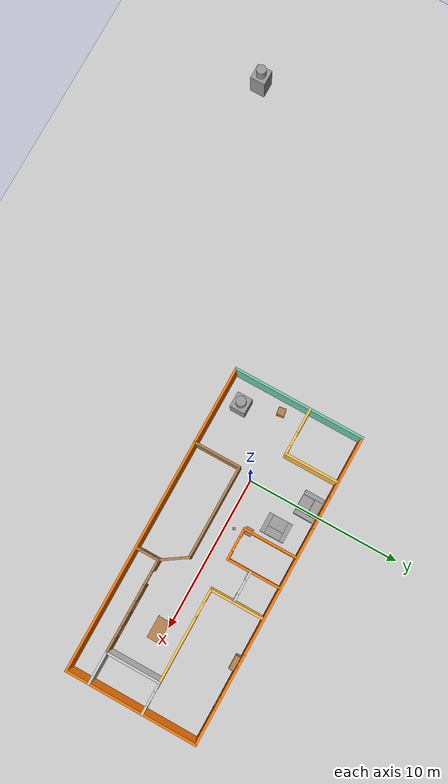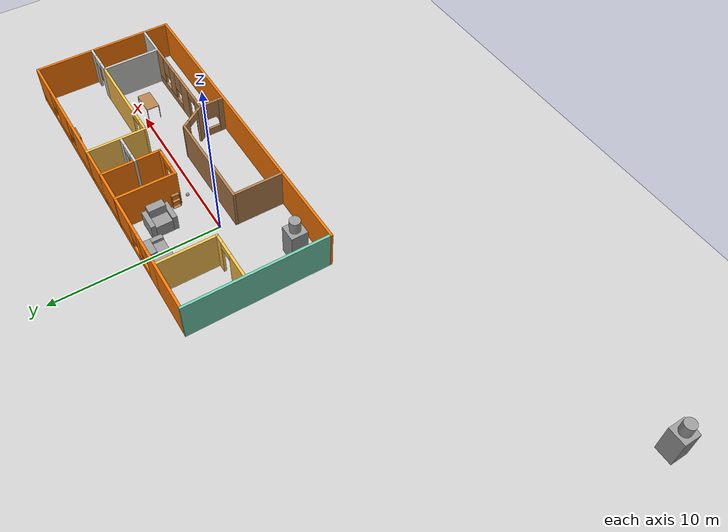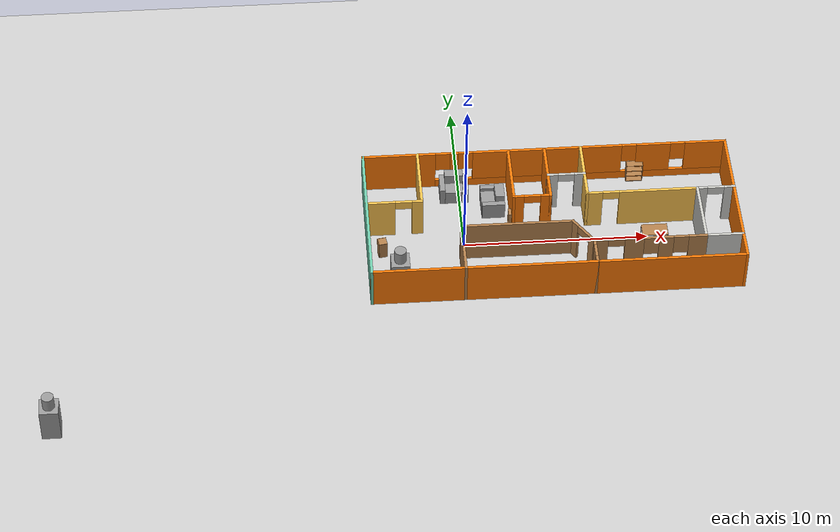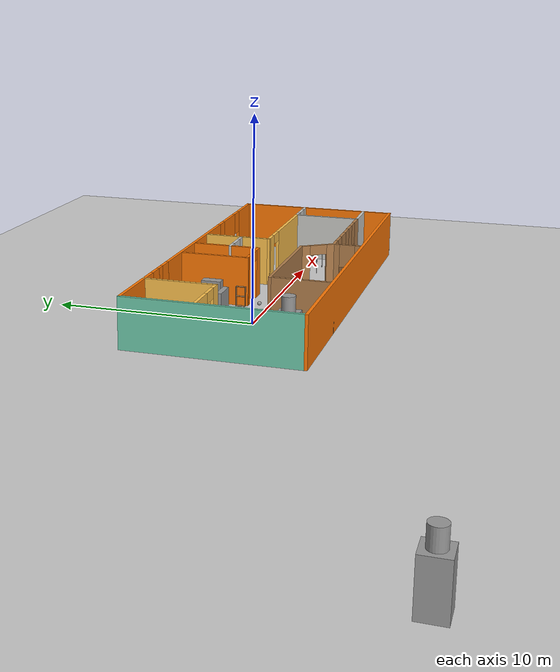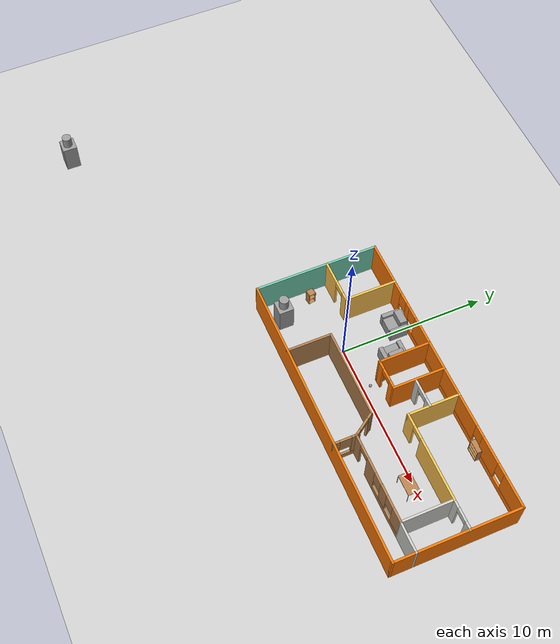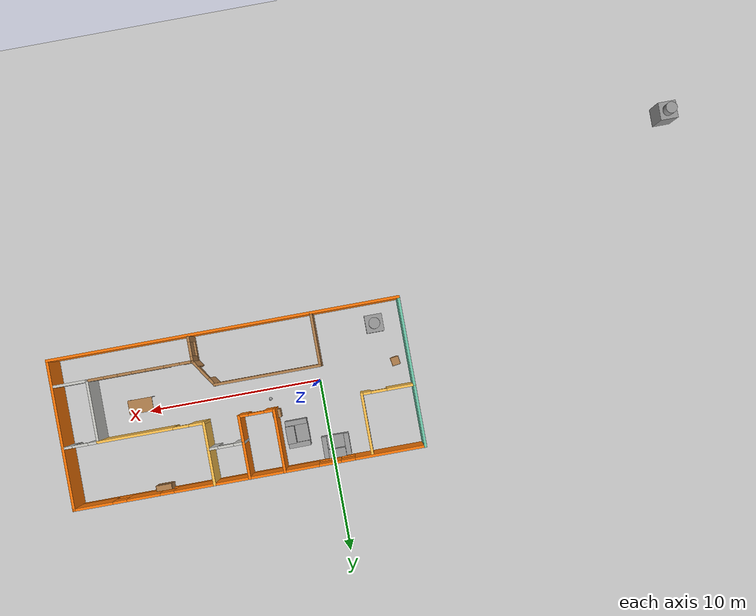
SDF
<sdf version="1.6">
 <world name="default">
  <plugin name="message" filename="../build/libmessage.so"/>
  <light name="sun" type="directional">
   <pose>0 0 10 0 -0 0</pose>
   <diffuse>0.8 0.8 0.8 1</diffuse>
   <specular>0.1 0.1 0.1 1</specular>
   <attenuation>
    <range>1000</range>
    <constant>0.9</constant>
    <linear>0.01</linear>
    <quadratic>0.001</quadratic>
   </attenuation>
   <direction>-0.5 0.5 -1</direction>
  </light>
  <model name="ground_plane">
   <static>1</static>
   <link name="link">
    <collision name="collision">
     <geometry><plane><normal>0 0 1</normal><size>100 100</size></plane></geometry>
     <surface><friction><ode><mu>100</mu><mu2>50</mu2></ode></friction></surface>
    </collision>
    <visual name="visual">
     <cast_shadows>0</cast_shadows>
     <geometry><plane><normal>0 0 1</normal><size>100 100</size></plane></geometry>
     <material>
      <script><uri>file://media/materials/scripts/gazebo.material</uri><name>Gazebo/Grey</name></script>
     </material>
    </visual>
   </link>
  </model>
  <gravity>0 0 -9.8</gravity>
  <magnetic_field>6e-06 2.3e-05 -4.2e-05</magnetic_field>
  <atmosphere type="adiabatic"/>
  <physics name="default_physics" default="0" type="ode">
   <max_step_size>0.001</max_step_size>
   <real_time_factor>1</real_time_factor>
   <real_time_update_rate>1000</real_time_update_rate>
  </physics>
  <scene><ambient>0.4 0.4 0.4 1</ambient><background>0.7 0.7 0.7 1</background><shadows>1</shadows></scene>
  <spherical_coordinates>
   <surface_model>EARTH_WGS84</surface_model>
   <latitude_deg>0</latitude_deg>
   <longitude_deg>0</longitude_deg>
   <elevation>0</elevation>
   <heading_deg>0</heading_deg>
  </spherical_coordinates>
  <model name="small_sofa_0">
   <link name="link_0">
    <pose>-0.343323 0 0.163374 0 -0 0</pose>
    <inertial>
     <mass>0.692242</mass>
     <inertia>
      <ixx>0.165884</ixx>
      <ixy>0</ixy>
      <ixz>0</ixz>
      <iyy>0.123566</iyy>
      <iyz>0</iyz>
      <izz>0.0719312</izz>
     </inertia>
    </inertial>
    <visual name="visual">
     <geometry><box><size>0.50663 0.995112 1.37309</size></box></geometry>
     <material>
      <lighting>1</lighting>
      <script><uri>file://media/materials/scripts/gazebo.material</uri><name>Gazebo/Grey</name></script>
      <ambient>0.3 0.3 0.3 1</ambient>
      <diffuse>0.7 0.7 0.7 1</diffuse>
      <specular>0.01 0.01 0.01 1</specular>
      <emissive>0 0 0 1</emissive>
     </material>
    </visual>
    <collision name="collision">
     <geometry><box><size>0.50663 0.995112 1.37309</size></box></geometry>
     <surface>
      <friction>
       <ode><mu>1</mu><mu2>1</mu2><fdir1>0 0 0</fdir1><slip1>0</slip1><slip2>0</slip2></ode>
       <torsional>
        <coefficient>1</coefficient>
        <patch_radius>0</patch_radius>
        <surface_radius>0</surface_radius>
        <use_patch_radius>1</use_patch_radius>
        <ode><slip>0</slip></ode>
       </torsional>
      </friction>
      <bounce><restitution_coefficient>0</restitution_coefficient><threshold>1e+06</threshold></bounce>
      <contact>
       <collide_without_contact>0</collide_without_contact>
       <collide_without_contact_bitmask>1</collide_without_contact_bitmask>
       <collide_bitmask>1</collide_bitmask>
       <ode>
        <soft_cfm>0</soft_cfm>
        <soft_erp>0.2</soft_erp>
        <kp>1e+13</kp>
        <kd>1</kd>
        <max_vel>0.01</max_vel>
        <min_depth>0</min_depth>
       </ode>
       <bullet>
        <split_impulse>1</split_impulse>
        <split_impulse_penetration_threshold>-0.01</split_impulse_penetration_threshold>
        <soft_cfm>0</soft_cfm>
        <soft_erp>0.2</soft_erp>
        <kp>1e+13</kp>
        <kd>1</kd>
       </bullet>
      </contact>
     </surface>
    </collision>
   </link>
   <link name="link_0_clone">
    <pose>0.284589 0 -0.11703 0 -0 0</pose>
    <inertial>
     <mass>0.605576</mass>
     <inertia>
      <ixx>0.0832689</ixx>
      <ixy>0</ixy>
      <ixz>0</ixz>
      <iyy>0.0616212</iyy>
      <iyz>0</iyz>
      <izz>0.0782979</izz>
     </inertia>
    </inertial>
    <visual name="visual">
     <geometry><box><size>0.749193 0.995112 0.812285</size></box></geometry>
     <material>
      <lighting>1</lighting>
      <script><uri>file://media/materials/scripts/gazebo.material</uri><name>Gazebo/Grey</name></script>
      <ambient>0.3 0.3 0.3 1</ambient>
      <diffuse>0.7 0.7 0.7 1</diffuse>
      <specular>0.01 0.01 0.01 1</specular>
      <emissive>0 0 0 1</emissive>
      <shader type="pixel"/>
     </material>
    </visual>
    <collision name="collision">
     <geometry><box><size>0.749193 0.995112 0.812285</size></box></geometry>
     <surface>
      <friction>
       <ode><mu>1</mu><mu2>1</mu2><fdir1>0 0 0</fdir1><slip1>0</slip1><slip2>0</slip2></ode>
       <torsional>
        <coefficient>1</coefficient>
        <patch_radius>0</patch_radius>
        <surface_radius>0</surface_radius>
        <use_patch_radius>1</use_patch_radius>
        <ode><slip>0</slip></ode>
       </torsional>
      </friction>
      <bounce><restitution_coefficient>0</restitution_coefficient><threshold>1e+06</threshold></bounce>
      <contact>
       <collide_without_contact>0</collide_without_contact>
       <collide_without_contact_bitmask>1</collide_without_contact_bitmask>
       <collide_bitmask>1</collide_bitmask>
       <ode>
        <soft_cfm>0</soft_cfm>
        <soft_erp>0.2</soft_erp>
        <kp>1e+13</kp>
        <kd>1</kd>
        <max_vel>0.01</max_vel>
        <min_depth>0</min_depth>
       </ode>
       <bullet>
        <split_impulse>1</split_impulse>
        <split_impulse_penetration_threshold>-0.01</split_impulse_penetration_threshold>
        <soft_cfm>0</soft_cfm>
        <soft_erp>0.2</soft_erp>
        <kp>1e+13</kp>
        <kd>1</kd>
       </bullet>
      </contact>
     </surface>
    </collision>
   </link>
   <link name="link_1">
    <pose>0.029367 0.639671 -0.023172 0 -0 0</pose>
    <inertial>
     <mass>0.355854</mass>
     <inertia>
      <ixx>0.0320502</ixx>
      <ixy>0</ixy>
      <ixz>0</ixz>
      <iyy>0.0761386</iyy>
      <iyz>0</iyz>
      <izz>0.0488797</izz>
     </inertia>
    </inertial>
    <visual name="visual">
     <geometry><box><size>1.25201 0.284226 1</size></box></geometry>
     <material>
      <lighting>1</lighting>
      <script><uri>file://media/materials/scripts/gazebo.material</uri><name>Gazebo/Grey</name></script>
      <ambient>0.3 0.3 0.3 1</ambient>
      <diffuse>0.7 0.7 0.7 1</diffuse>
      <specular>0.01 0.01 0.01 1</specular>
      <emissive>0 0 0 1</emissive>
     </material>
    </visual>
    <collision name="collision">
     <geometry><box><size>1.25201 0.284226 1</size></box></geometry>
     <surface>
      <friction>
       <ode><mu>1</mu><mu2>1</mu2><fdir1>0 0 0</fdir1><slip1>0</slip1><slip2>0</slip2></ode>
       <torsional>
        <coefficient>1</coefficient>
        <patch_radius>0</patch_radius>
        <surface_radius>0</surface_radius>
        <use_patch_radius>1</use_patch_radius>
        <ode><slip>0</slip></ode>
       </torsional>
      </friction>
      <bounce><restitution_coefficient>0</restitution_coefficient><threshold>1e+06</threshold></bounce>
      <contact>
       <collide_without_contact>0</collide_without_contact>
       <collide_without_contact_bitmask>1</collide_without_contact_bitmask>
       <collide_bitmask>1</collide_bitmask>
       <ode>
        <soft_cfm>0</soft_cfm>
        <soft_erp>0.2</soft_erp>
        <kp>1e+13</kp>
        <kd>1</kd>
        <max_vel>0.01</max_vel>
        <min_depth>0</min_depth>
       </ode>
       <bullet>
        <split_impulse>1</split_impulse>
        <split_impulse_penetration_threshold>-0.01</split_impulse_penetration_threshold>
        <soft_cfm>0</soft_cfm>
        <soft_erp>0.2</soft_erp>
        <kp>1e+13</kp>
        <kd>1</kd>
       </bullet>
      </contact>
     </surface>
    </collision>
   </link>
   <link name="link_1_clone">
    <pose>0.029367 -0.639671 -0.023172 0 -0 0</pose>
    <inertial>
     <mass>0.355854</mass>
     <inertia>
      <ixx>0.0320502</ixx>
      <ixy>0</ixy>
      <ixz>0</ixz>
      <iyy>0.0761386</iyy>
      <iyz>0</iyz>
      <izz>0.0488797</izz>
     </inertia>
    </inertial>
    <visual name="visual">
     <geometry><box><size>1.25201 0.284226 1</size></box></geometry>
     <material>
      <lighting>1</lighting>
      <script><uri>file://media/materials/scripts/gazebo.material</uri><name>Gazebo/Grey</name></script>
      <ambient>0.3 0.3 0.3 1</ambient>
      <diffuse>0.7 0.7 0.7 1</diffuse>
      <specular>0.01 0.01 0.01 1</specular>
      <emissive>0 0 0 1</emissive>
      <shader type="pixel"/>
     </material>
    </visual>
    <collision name="collision">
     <geometry><box><size>1.25201 0.284226 1</size></box></geometry>
     <surface>
      <friction>
       <ode><mu>1</mu><mu2>1</mu2><fdir1>0 0 0</fdir1><slip1>0</slip1><slip2>0</slip2></ode>
       <torsional>
        <coefficient>1</coefficient>
        <patch_radius>0</patch_radius>
        <surface_radius>0</surface_radius>
        <use_patch_radius>1</use_patch_radius>
        <ode><slip>0</slip></ode>
       </torsional>
      </friction>
      <bounce><restitution_coefficient>0</restitution_coefficient><threshold>1e+06</threshold></bounce>
      <contact>
       <collide_without_contact>0</collide_without_contact>
       <collide_without_contact_bitmask>1</collide_without_contact_bitmask>
       <collide_bitmask>1</collide_bitmask>
       <ode>
        <soft_cfm>0</soft_cfm>
        <soft_erp>0.2</soft_erp>
        <kp>1e+13</kp>
        <kd>1</kd>
        <max_vel>0.01</max_vel>
        <min_depth>0</min_depth>
       </ode>
       <bullet>
        <split_impulse>1</split_impulse>
        <split_impulse_penetration_threshold>-0.01</split_impulse_penetration_threshold>
        <soft_cfm>0</soft_cfm>
        <soft_erp>0.2</soft_erp>
        <kp>1e+13</kp>
        <kd>1</kd>
       </bullet>
      </contact>
     </surface>
    </collision>
   </link>
   <joint name="link_0_JOINT_1" type="revolute">
    <parent>link_0</parent>
    <child>link_1_clone</child>
    <axis>
     <xyz>1 0 0</xyz>
     <use_parent_model_frame>0</use_parent_model_frame>
     <limit>
      <lower>-1.79769e+308</lower>
      <upper>1.79769e+308</upper>
      <effort>-1</effort>
      <velocity>-1</velocity>
     </limit>
     <dynamics>
      <spring_reference>0</spring_reference>
      <spring_stiffness>0</spring_stiffness>
      <damping>0</damping>
     </dynamics>
    </axis>
    <physics>
     <ode><limit><cfm>0</cfm><erp>0.2</erp></limit><suspension><cfm>0</cfm><erp>0.2</erp></suspension></ode>
    </physics>
   </joint>
   <joint name="link_0_JOINT_2" type="revolute">
    <parent>link_0</parent>
    <child>link_0_clone</child>
    <axis>
     <xyz>1 0 0</xyz>
     <use_parent_model_frame>0</use_parent_model_frame>
     <limit>
      <lower>-1.79769e+308</lower>
      <upper>1.79769e+308</upper>
      <effort>-1</effort>
      <velocity>-1</velocity>
     </limit>
     <dynamics>
      <spring_reference>0</spring_reference>
      <spring_stiffness>0</spring_stiffness>
      <damping>0</damping>
     </dynamics>
    </axis>
    <physics>
     <ode><limit><cfm>0</cfm><erp>0.2</erp></limit><suspension><cfm>0</cfm><erp>0.2</erp></suspension></ode>
    </physics>
   </joint>
   <joint name="link_1_JOINT_0" type="revolute">
    <parent>link_1</parent>
    <child>link_0</child>
    <axis>
     <xyz>1 0 0</xyz>
     <use_parent_model_frame>0</use_parent_model_frame>
     <limit>
      <lower>-1.79769e+308</lower>
      <upper>1.79769e+308</upper>
      <effort>-1</effort>
      <velocity>-1</velocity>
     </limit>
     <dynamics>
      <spring_reference>0</spring_reference>
      <spring_stiffness>0</spring_stiffness>
      <damping>0</damping>
     </dynamics>
    </axis>
    <physics>
     <ode><limit><cfm>0</cfm><erp>0.2</erp></limit><suspension><cfm>0</cfm><erp>0.2</erp></suspension></ode>
    </physics>
   </joint>
   <static>0</static>
   <pose>-0.300984 3.85056 0.523174 5e-06 -0 -1.57872</pose>
  </model>
  <model name="Building">
   <pose>4.7412 0.361822 0 0 -0 0</pose>
   <link name="Wall_0">
    <collision name="Wall_0_Collision">
     <geometry><box><size>20.15 0.15 2.5</size></box></geometry>
     <pose>0 0 1.25 0 -0 0</pose>
    </collision>
    <visual name="Wall_0_Visual">
     <pose>0 0 1.25 0 -0 0</pose>
     <geometry><box><size>20.15 0.15 2.5</size></box></geometry>
     <material>
      <script><uri>file://media/materials/scripts/gazebo.material</uri><name>Gazebo/Grey</name></script>
      <ambient>0.996078 0.47451 0.0196078 1</ambient>
     </material>
    </visual>
    <pose>0 -4.25 0 0 -0 0</pose>
   </link>
   <link name="Wall_10">
    <pose>-8.5 0.75 0 0 -0 3.14159</pose>
    <visual name="Wall_10_Visual_0">
     <pose>-1.26846 0 1.25 0 -0 0</pose>
     <geometry><box><size>0.613081 0.15 2.5</size></box></geometry>
     <material>
      <script><uri>file://media/materials/scripts/gazebo.material</uri><name>Gazebo/Grey</name></script>
      <ambient>1 0.764706 0.305882 1</ambient>
     </material>
    </visual>
    <collision name="Wall_10_Collision_0">
     <geometry><box><size>0.613081 0.15 2.5</size></box></geometry>
     <pose>-1.26846 0 1.25 0 -0 0</pose>
    </collision>
    <visual name="Wall_10_Visual_1">
     <pose>0.75654 0 1.25 0 -0 0</pose>
     <geometry><box><size>1.63692 0.15 2.5</size></box></geometry>
     <material>
      <script><uri>file://media/materials/scripts/gazebo.material</uri><name>Gazebo/Grey</name></script>
      <ambient>1 0.764706 0.305882 1</ambient>
     </material>
    </visual>
    <collision name="Wall_10_Collision_1">
     <geometry><box><size>1.63692 0.15 2.5</size></box></geometry>
     <pose>0.75654 0 1.25 0 -0 0</pose>
    </collision>
    <visual name="Wall_10_Visual_2">
     <pose>-0.511919 0 2.25 0 -0 0</pose>
     <geometry><box><size>0.9 0.15 0.5</size></box></geometry>
     <material>
      <script><uri>file://media/materials/scripts/gazebo.material</uri><name>Gazebo/Grey</name></script>
      <ambient>1 0.764706 0.305882 1</ambient>
     </material>
    </visual>
    <collision name="Wall_10_Collision_2">
     <geometry><box><size>0.9 0.15 0.5</size></box></geometry>
     <pose>-0.511919 0 2.25 0 -0 0</pose>
    </collision>
   </link>
   <link name="Wall_12">
    <collision name="Wall_12_Collision">
     <geometry><box><size>3.65 0.15 2.5</size></box></geometry>
     <pose>0 0 1.25 0 -0 0</pose>
    </collision>
    <visual name="Wall_12_Visual">
     <pose>0 0 1.25 0 -0 0</pose>
     <geometry><box><size>3.65 0.15 2.5</size></box></geometry>
     <material>
      <script><uri>file://media/materials/scripts/gazebo.material</uri><name>Gazebo/Grey</name></script>
      <ambient>0.996078 0.47451 0.0196078 1</ambient>
     </material>
    </visual>
    <pose>-2 2.5 0 0 0 -1.5708</pose>
   </link>
   <link name="Wall_14">
    <collision name="Wall_14_Collision">
     <geometry><box><size>3.65 0.15 2.5</size></box></geometry>
     <pose>0 0 1.25 0 -0 0</pose>
    </collision>
    <visual name="Wall_14_Visual">
     <pose>0 0 1.25 0 -0 0</pose>
     <geometry><box><size>3.65 0.15 2.5</size></box></geometry>
     <material>
      <script><uri>file://media/materials/scripts/gazebo.material</uri><name>Gazebo/Grey</name></script>
      <ambient>1 0.764706 0.305882 1</ambient>
     </material>
    </visual>
    <pose>2 2.5 0 0 -0 1.5708</pose>
   </link>
   <link name="Wall_16">
    <pose>-1 0.75 0 0 -0 0</pose>
    <visual name="Wall_16_Visual_0">
     <pose>-0.758614 0 1.25 0 -0 0</pose>
     <geometry><box><size>0.632771 0.15 2.5</size></box></geometry>
     <material>
      <script><uri>file://media/materials/scripts/gazebo.material</uri><name>Gazebo/Grey</name></script>
      <ambient>0.996078 0.47451 0.0196078 1</ambient>
     </material>
    </visual>
    <collision name="Wall_16_Collision_0">
     <geometry><box><size>0.632771 0.15 2.5</size></box></geometry>
     <pose>-0.758614 0 1.25 0 -0 0</pose>
    </collision>
    <visual name="Wall_16_Visual_1">
     <pose>0.766386 0 1.25 0 -0 0</pose>
     <geometry><box><size>0.617229 0.15 2.5</size></box></geometry>
     <material>
      <script><uri>file://media/materials/scripts/gazebo.material</uri><name>Gazebo/Grey</name></script>
      <ambient>0.996078 0.47451 0.0196078 1</ambient>
     </material>
    </visual>
    <collision name="Wall_16_Collision_1">
     <geometry><box><size>0.617229 0.15 2.5</size></box></geometry>
     <pose>0.766386 0 1.25 0 -0 0</pose>
    </collision>
    <visual name="Wall_16_Visual_2">
     <pose>0.007771 0 2.25 0 -0 0</pose>
     <geometry><box><size>0.9 0.15 0.5</size></box></geometry>
     <material>
      <script><uri>file://media/materials/scripts/gazebo.material</uri><name>Gazebo/Grey</name></script>
      <ambient>0.996078 0.47451 0.0196078 1</ambient>
     </material>
    </visual>
    <collision name="Wall_16_Collision_2">
     <geometry><box><size>0.9 0.15 0.5</size></box></geometry>
     <pose>0.007771 0 2.25 0 -0 0</pose>
    </collision>
   </link>
   <link name="Wall_17">
    <collision name="Wall_17_Collision">
     <geometry><box><size>3.65 0.15 2.5</size></box></geometry>
     <pose>0 0 1.25 0 -0 0</pose>
    </collision>
    <visual name="Wall_17_Visual">
     <pose>0 0 1.25 0 -0 0</pose>
     <geometry><box><size>3.65 0.15 2.5</size></box></geometry>
     <material>
      <script><uri>file://media/materials/scripts/gazebo.material</uri><name>Gazebo/Grey</name></script>
      <ambient>0.996078 0.47451 0.0196078 1</ambient>
     </material>
    </visual>
    <pose>0 2.5 0 0 -0 1.5708</pose>
   </link>
   <link name="Wall_19">
    <pose>1 2.25 0 0 -0 0</pose>
    <visual name="Wall_19_Visual_0">
     <pose>-0.761107 0 1.25 0 -0 0</pose>
     <geometry><box><size>0.627787 0.15 2.5</size></box></geometry>
     <material>
      <script><uri>file://media/materials/scripts/gazebo.material</uri><name>Gazebo/CeilingTiled</name></script>
      <ambient>1 0.764706 0.305882 1</ambient>
     </material>
    </visual>
    <collision name="Wall_19_Collision_0">
     <geometry><box><size>0.627787 0.15 2.5</size></box></geometry>
     <pose>-0.761107 0 1.25 0 -0 0</pose>
    </collision>
    <visual name="Wall_19_Visual_1">
     <pose>0.763893 0 1.25 0 -0 0</pose>
     <geometry><box><size>0.622213 0.15 2.5</size></box></geometry>
     <material>
      <script><uri>file://media/materials/scripts/gazebo.material</uri><name>Gazebo/CeilingTiled</name></script>
      <ambient>1 0.764706 0.305882 1</ambient>
     </material>
    </visual>
    <collision name="Wall_19_Collision_1">
     <geometry><box><size>0.622213 0.15 2.5</size></box></geometry>
     <pose>0.763893 0 1.25 0 -0 0</pose>
    </collision>
    <visual name="Wall_19_Visual_2">
     <pose>0.002787 0 2.25 0 -0 0</pose>
     <geometry><box><size>0.9 0.15 0.5</size></box></geometry>
     <material>
      <script><uri>file://media/materials/scripts/gazebo.material</uri><name>Gazebo/CeilingTiled</name></script>
      <ambient>1 0.764706 0.305882 1</ambient>
     </material>
    </visual>
    <collision name="Wall_19_Collision_2">
     <geometry><box><size>0.9 0.15 0.5</size></box></geometry>
     <pose>0.002787 0 2.25 0 -0 0</pose>
    </collision>
   </link>
   <link name="Wall_2">
    <collision name="Wall_2_Collision">
     <geometry><box><size>8.65 0.15 2.5</size></box></geometry>
     <pose>0 0 1.25 0 -0 0</pose>
    </collision>
    <visual name="Wall_2_Visual">
     <pose>0 0 1.25 0 -0 0</pose>
     <geometry><box><size>8.65 0.15 2.5</size></box></geometry>
     <material>
      <script><uri>file://media/materials/scripts/gazebo.material</uri><name>Gazebo/Grey</name></script>
      <ambient>0.435294 0.796078 0.67451 1</ambient>
     </material>
    </visual>
    <pose>-10 0 0 0 -0 1.5708</pose>
   </link>
   <link name="Wall_25">
    <collision name="Wall_25_Collision">
     <geometry><box><size>2.15 0.15 2.5</size></box></geometry>
     <pose>0 0 1.25 0 -0 0</pose>
    </collision>
    <visual name="Wall_25_Visual">
     <pose>0 0 1.25 0 -0 0</pose>
     <geometry><box><size>2.15 0.15 2.5</size></box></geometry>
     <material>
      <script><uri>file://media/materials/scripts/gazebo.material</uri><name>Gazebo/CeilingTiled</name></script>
      <ambient>1 1 1 1</ambient>
     </material>
    </visual>
    <pose>9 -2.75 0 0 -0 0</pose>
   </link>
   <link name="Wall_27">
    <pose>5 0.75 0 0 -0 0</pose>
    <visual name="Wall_27_Visual_0">
     <pose>-2.6173 0 1.25 0 -0 0</pose>
     <geometry><box><size>0.915403 0.15 2.5</size></box></geometry>
     <material>
      <script><uri>file://media/materials/scripts/gazebo.material</uri><name>Gazebo/Grey</name></script>
      <ambient>1 0.764706 0.305882 1</ambient>
     </material>
    </visual>
    <collision name="Wall_27_Collision_0">
     <geometry><box><size>0.915403 0.15 2.5</size></box></geometry>
     <pose>-2.6173 0 1.25 0 -0 0</pose>
    </collision>
    <visual name="Wall_27_Visual_1">
     <pose>0.907702 0 1.25 0 -0 0</pose>
     <geometry><box><size>4.3346 0.15 2.5</size></box></geometry>
     <material>
      <script><uri>file://media/materials/scripts/gazebo.material</uri><name>Gazebo/Grey</name></script>
      <ambient>1 0.764706 0.305882 1</ambient>
     </material>
    </visual>
    <collision name="Wall_27_Collision_1">
     <geometry><box><size>4.3346 0.15 2.5</size></box></geometry>
     <pose>0.907702 0 1.25 0 -0 0</pose>
    </collision>
    <visual name="Wall_27_Visual_2">
     <pose>-1.7096 0 2.25 0 -0 0</pose>
     <geometry><box><size>0.9 0.15 0.5</size></box></geometry>
     <material>
      <script><uri>file://media/materials/scripts/gazebo.material</uri><name>Gazebo/Grey</name></script>
      <ambient>1 0.764706 0.305882 1</ambient>
     </material>
    </visual>
    <collision name="Wall_27_Collision_2">
     <geometry><box><size>0.9 0.15 0.5</size></box></geometry>
     <pose>-1.7096 0 2.25 0 -0 0</pose>
    </collision>
   </link>
   <link name="Wall_29">
    <collision name="Wall_29_Collision">
     <geometry><box><size>3.65 0.15 2.5</size></box></geometry>
     <pose>0 0 1.25 0 -0 0</pose>
    </collision>
    <visual name="Wall_29_Visual">
     <pose>0 0 1.25 0 -0 0</pose>
     <geometry><box><size>3.65 0.15 2.5</size></box></geometry>
     <material>
      <script><uri>file://media/materials/scripts/gazebo.material</uri><name>Gazebo/CeilingTiled</name></script>
      <ambient>1 1 1 1</ambient>
     </material>
    </visual>
    <pose>8 -1 0 0 0 -1.5708</pose>
   </link>
   <link name="Wall_31">
    <pose>9 0.75 0 0 -0 0</pose>
    <visual name="Wall_31_Visual_0">
     <pose>-0.757777 0 1.25 0 -0 0</pose>
     <geometry><box><size>0.634446 0.15 2.5</size></box></geometry>
     <material>
      <script><uri>file://media/materials/scripts/gazebo.material</uri><name>Gazebo/CeilingTiled</name></script>
      <ambient>1 1 1 1</ambient>
     </material>
    </visual>
    <collision name="Wall_31_Collision_0">
     <geometry><box><size>0.634446 0.15 2.5</size></box></geometry>
     <pose>-0.757777 0 1.25 0 -0 0</pose>
    </collision>
    <visual name="Wall_31_Visual_1">
     <pose>0.767223 0 1.25 0 -0 0</pose>
     <geometry><box><size>0.615554 0.15 2.5</size></box></geometry>
     <material>
      <script><uri>file://media/materials/scripts/gazebo.material</uri><name>Gazebo/CeilingTiled</name></script>
      <ambient>1 1 1 1</ambient>
     </material>
    </visual>
    <collision name="Wall_31_Collision_1">
     <geometry><box><size>0.615554 0.15 2.5</size></box></geometry>
     <pose>0.767223 0 1.25 0 -0 0</pose>
    </collision>
    <visual name="Wall_31_Visual_2">
     <pose>0.009446 0 2.25 0 -0 0</pose>
     <geometry><box><size>0.9 0.15 0.5</size></box></geometry>
     <material>
      <script><uri>file://media/materials/scripts/gazebo.material</uri><name>Gazebo/CeilingTiled</name></script>
      <ambient>1 1 1 1</ambient>
     </material>
    </visual>
    <collision name="Wall_31_Collision_2">
     <geometry><box><size>0.9 0.15 0.5</size></box></geometry>
     <pose>0.009446 0 2.25 0 -0 0</pose>
    </collision>
   </link>
   <link name="Wall_35">
    <collision name="Wall_35_Collision">
     <geometry><box><size>3.15 0.15 2.5</size></box></geometry>
     <pose>0 0 1.25 0 -0 0</pose>
    </collision>
    <visual name="Wall_35_Visual">
     <pose>0 0 1.25 0 -0 0</pose>
     <geometry><box><size>3.15 0.15 2.5</size></box></geometry>
     <material>
      <script><uri>file://media/materials/scripts/gazebo.material</uri><name>Gazebo/Wood</name></script>
      <ambient>0.996078 0.47451 0.0196078 1</ambient>
     </material>
    </visual>
    <pose>-5 -2.75 0 0 0 -1.5708</pose>
   </link>
   <link name="Wall_37">
    <collision name="Wall_37_Collision">
     <geometry><box><size>6.15 0.15 2.5</size></box></geometry>
     <pose>0 0 1.25 0 -0 0</pose>
    </collision>
    <visual name="Wall_37_Visual">
     <pose>0 0 1.25 0 -0 0</pose>
     <geometry><box><size>6.15 0.15 2.5</size></box></geometry>
     <material>
      <script><uri>file://media/materials/scripts/gazebo.material</uri><name>Gazebo/Wood</name></script>
      <ambient>0.996078 0.47451 0.0196078 1</ambient>
     </material>
    </visual>
    <pose>-2 -1.25 0 0 -0 0</pose>
   </link>
   <link name="Wall_39">
    <pose>2 -3.5 0 0 -0 1.5708</pose>
    <visual name="Wall_39_Visual_0">
     <pose>-0.594128 0 1.25 0 -0 0</pose>
     <geometry><box><size>0.461743 0.15 2.5</size></box></geometry>
     <material>
      <script><uri>file://media/materials/scripts/gazebo.material</uri><name>Gazebo/Wood</name></script>
      <ambient>0.996078 0.47451 0.0196078 1</ambient>
     </material>
    </visual>
    <collision name="Wall_39_Collision_0">
     <geometry><box><size>0.461743 0.15 2.5</size></box></geometry>
     <pose>-0.594128 0 1.25 0 -0 0</pose>
    </collision>
    <visual name="Wall_39_Visual_1">
     <pose>0.230872 0 0.25 0 -0 0</pose>
     <geometry><box><size>1.18826 0.15 0.5</size></box></geometry>
     <material>
      <script><uri>file://media/materials/scripts/gazebo.material</uri><name>Gazebo/Wood</name></script>
      <ambient>0.996078 0.47451 0.0196078 1</ambient>
     </material>
    </visual>
    <collision name="Wall_39_Collision_1">
     <geometry><box><size>1.18826 0.15 0.5</size></box></geometry>
     <pose>0.230872 0 0.25 0 -0 0</pose>
    </collision>
    <visual name="Wall_39_Visual_2">
     <pose>0.630872 0 1.5 0 -0 0</pose>
     <geometry><box><size>0.388257 0.15 2</size></box></geometry>
     <material>
      <script><uri>file://media/materials/scripts/gazebo.material</uri><name>Gazebo/Wood</name></script>
      <ambient>0.996078 0.47451 0.0196078 1</ambient>
     </material>
    </visual>
    <collision name="Wall_39_Collision_2">
     <geometry><box><size>0.388257 0.15 2</size></box></geometry>
     <pose>0.630872 0 1.5 0 -0 0</pose>
    </collision>
    <visual name="Wall_39_Visual_3">
     <pose>0.036743 0 1.9 0 -0 0</pose>
     <geometry><box><size>0.8 0.15 1.2</size></box></geometry>
     <material>
      <script><uri>file://media/materials/scripts/gazebo.material</uri><name>Gazebo/Wood</name></script>
      <ambient>0.996078 0.47451 0.0196078 1</ambient>
     </material>
    </visual>
    <collision name="Wall_39_Collision_3">
     <geometry><box><size>0.8 0.15 1.2</size></box></geometry>
     <pose>0.036743 0 1.9 0 -0 0</pose>
    </collision>
   </link>
   <link name="Wall_4">
    <pose>0 4.25 0 0 -0 0</pose>
    <visual name="Wall_4_Visual_0">
     <pose>-8.04057 0 1.25 0 -0 0</pose>
     <geometry><box><size>4.06886 0.15 2.5</size></box></geometry>
     <material>
      <script><uri>file://media/materials/scripts/gazebo.material</uri><name>Gazebo/Grey</name></script>
      <ambient>0.996078 0.47451 0.0196078 1</ambient>
     </material>
    </visual>
    <collision name="Wall_4_Collision_0">
     <geometry><box><size>4.06886 0.15 2.5</size></box></geometry>
     <pose>-8.04057 0 1.25 0 -0 0</pose>
    </collision>
    <visual name="Wall_4_Visual_1">
     <pose>2.03443 0 0.25 0 -0 0</pose>
     <geometry><box><size>16.0811 0.15 0.5</size></box></geometry>
     <material>
      <script><uri>file://media/materials/scripts/gazebo.material</uri><name>Gazebo/Grey</name></script>
      <ambient>0.996078 0.47451 0.0196078 1</ambient>
     </material>
    </visual>
    <collision name="Wall_4_Collision_1">
     <geometry><box><size>16.0811 0.15 0.5</size></box></geometry>
     <pose>2.03443 0 0.25 0 -0 0</pose>
    </collision>
    <visual name="Wall_4_Visual_2">
     <pose>-4.97904 0 1.5 0 -0 0</pose>
     <geometry><box><size>0.4542 0.15 2</size></box></geometry>
     <material>
      <script><uri>file://media/materials/scripts/gazebo.material</uri><name>Gazebo/Grey</name></script>
      <ambient>0.996078 0.47451 0.0196078 1</ambient>
     </material>
    </visual>
    <collision name="Wall_4_Collision_2">
     <geometry><box><size>0.4542 0.15 2</size></box></geometry>
     <pose>-4.97904 0 1.5 0 -0 0</pose>
    </collision>
    <visual name="Wall_4_Visual_3">
     <pose>0.175411 0 1.5 0 -0 0</pose>
     <geometry><box><size>8.25471 0.15 2</size></box></geometry>
     <material>
      <script><uri>file://media/materials/scripts/gazebo.material</uri><name>Gazebo/Grey</name></script>
      <ambient>0.996078 0.47451 0.0196078 1</ambient>
     </material>
    </visual>
    <collision name="Wall_4_Collision_3">
     <geometry><box><size>8.25471 0.15 2</size></box></geometry>
     <pose>0.175411 0 1.5 0 -0 0</pose>
    </collision>
    <visual name="Wall_4_Visual_4">
     <pose>6.04873 0 1.5 0 -0 0</pose>
     <geometry><box><size>1.89194 0.15 2</size></box></geometry>
     <material>
      <script><uri>file://media/materials/scripts/gazebo.material</uri><name>Gazebo/Grey</name></script>
      <ambient>0.996078 0.47451 0.0196078 1</ambient>
     </material>
    </visual>
    <collision name="Wall_4_Collision_4">
     <geometry><box><size>1.89194 0.15 2</size></box></geometry>
     <pose>6.04873 0 1.5 0 -0 0</pose>
    </collision>
    <visual name="Wall_4_Visual_5">
     <pose>8.93485 0 1.5 0 -0 0</pose>
     <geometry><box><size>2.2803 0.15 2</size></box></geometry>
     <material>
      <script><uri>file://media/materials/scripts/gazebo.material</uri><name>Gazebo/Grey</name></script>
      <ambient>0.996078 0.47451 0.0196078 1</ambient>
     </material>
    </visual>
    <collision name="Wall_4_Collision_5">
     <geometry><box><size>2.2803 0.15 2</size></box></geometry>
     <pose>8.93485 0 1.5 0 -0 0</pose>
    </collision>
    <visual name="Wall_4_Visual_6">
     <pose>-5.60614 0 1.9 0 -0 0</pose>
     <geometry><box><size>0.8 0.15 1.2</size></box></geometry>
     <material>
      <script><uri>file://media/materials/scripts/gazebo.material</uri><name>Gazebo/Grey</name></script>
      <ambient>0.996078 0.47451 0.0196078 1</ambient>
     </material>
    </visual>
    <collision name="Wall_4_Collision_6">
     <geometry><box><size>0.8 0.15 1.2</size></box></geometry>
     <pose>-5.60614 0 1.9 0 -0 0</pose>
    </collision>
    <visual name="Wall_4_Visual_7">
     <pose>-4.35194 0 1.9 0 -0 0</pose>
     <geometry><box><size>0.8 0.15 1.2</size></box></geometry>
     <material>
      <script><uri>file://media/materials/scripts/gazebo.material</uri><name>Gazebo/Grey</name></script>
      <ambient>0.996078 0.47451 0.0196078 1</ambient>
     </material>
    </visual>
    <collision name="Wall_4_Collision_7">
     <geometry><box><size>0.8 0.15 1.2</size></box></geometry>
     <pose>-4.35194 0 1.9 0 -0 0</pose>
    </collision>
    <visual name="Wall_4_Visual_8">
     <pose>4.70276 0 1.9 0 -0 0</pose>
     <geometry><box><size>0.8 0.15 1.2</size></box></geometry>
     <material>
      <script><uri>file://media/materials/scripts/gazebo.material</uri><name>Gazebo/Grey</name></script>
      <ambient>0.996078 0.47451 0.0196078 1</ambient>
     </material>
    </visual>
    <collision name="Wall_4_Collision_8">
     <geometry><box><size>0.8 0.15 1.2</size></box></geometry>
     <pose>4.70276 0 1.9 0 -0 0</pose>
    </collision>
    <visual name="Wall_4_Visual_9">
     <pose>7.3947 0 1.9 0 -0 0</pose>
     <geometry><box><size>0.8 0.15 1.2</size></box></geometry>
     <material>
      <script><uri>file://media/materials/scripts/gazebo.material</uri><name>Gazebo/Grey</name></script>
      <ambient>0.996078 0.47451 0.0196078 1</ambient>
     </material>
    </visual>
    <collision name="Wall_4_Collision_9">
     <geometry><box><size>0.8 0.15 1.2</size></box></geometry>
     <pose>7.3947 0 1.9 0 -0 0</pose>
    </collision>
   </link>
   <link name="Wall_41">
    <pose>1.5 -2 0 0 0 -0.982794</pose>
    <visual name="Wall_41_Visual_0">
     <pose>-0.69985 0 1.25 0 -0 0</pose>
     <geometry><box><size>0.553076 0.15 2.5</size></box></geometry>
     <material>
      <script><uri>file://media/materials/scripts/gazebo.material</uri><name>Gazebo/Wood</name></script>
      <ambient>0.996078 0.47451 0.0196078 1</ambient>
     </material>
    </visual>
    <collision name="Wall_41_Collision_0">
     <geometry><box><size>0.553076 0.15 2.5</size></box></geometry>
     <pose>-0.69985 0 1.25 0 -0 0</pose>
    </collision>
    <visual name="Wall_41_Visual_1">
     <pose>0.726538 0 1.25 0 -0 0</pose>
     <geometry><box><size>0.4997 0.15 2.5</size></box></geometry>
     <material>
      <script><uri>file://media/materials/scripts/gazebo.material</uri><name>Gazebo/Wood</name></script>
      <ambient>0.996078 0.47451 0.0196078 1</ambient>
     </material>
    </visual>
    <collision name="Wall_41_Collision_1">
     <geometry><box><size>0.4997 0.15 2.5</size></box></geometry>
     <pose>0.726538 0 1.25 0 -0 0</pose>
    </collision>
    <visual name="Wall_41_Visual_2">
     <pose>0.026688 0 2.25 0 -0 0</pose>
     <geometry><box><size>0.9 0.15 0.5</size></box></geometry>
     <material>
      <script><uri>file://media/materials/scripts/gazebo.material</uri><name>Gazebo/Wood</name></script>
      <ambient>0.996078 0.47451 0.0196078 1</ambient>
     </material>
    </visual>
    <collision name="Wall_41_Collision_2">
     <geometry><box><size>0.9 0.15 0.5</size></box></geometry>
     <pose>0.026688 0 2.25 0 -0 0</pose>
    </collision>
   </link>
   <link name="Wall_43">
    <pose>5 -2.75 0 0 -0 0</pose>
    <visual name="Wall_43_Visual_0">
     <pose>-2.67402 0 1.25 0 -0 0</pose>
     <geometry><box><size>0.801957 0.15 2.5</size></box></geometry>
     <material>
      <script><uri>file://media/materials/scripts/gazebo.material</uri><name>Gazebo/Wood</name></script>
      <ambient>1 1 1 1</ambient>
     </material>
    </visual>
    <collision name="Wall_43_Collision_0">
     <geometry><box><size>0.801957 0.15 2.5</size></box></geometry>
     <pose>-2.67402 0 1.25 0 -0 0</pose>
    </collision>
    <visual name="Wall_43_Visual_1">
     <pose>-0.853736 0 1.25 0 -0 0</pose>
     <geometry><box><size>1.03861 0.15 2.5</size></box></geometry>
     <material>
      <script><uri>file://media/materials/scripts/gazebo.material</uri><name>Gazebo/Wood</name></script>
      <ambient>1 1 1 1</ambient>
     </material>
    </visual>
    <collision name="Wall_43_Collision_1">
     <geometry><box><size>1.03861 0.15 2.5</size></box></geometry>
     <pose>-0.853736 0 1.25 0 -0 0</pose>
    </collision>
    <visual name="Wall_43_Visual_2">
     <pose>1.37029 0 0.25 0 -0 0</pose>
     <geometry><box><size>3.40943 0.15 0.5</size></box></geometry>
     <material>
      <script><uri>file://media/materials/scripts/gazebo.material</uri><name>Gazebo/Wood</name></script>
      <ambient>1 1 1 1</ambient>
     </material>
    </visual>
    <collision name="Wall_43_Collision_2">
     <geometry><box><size>3.40943 0.15 0.5</size></box></geometry>
     <pose>1.37029 0 0.25 0 -0 0</pose>
    </collision>
    <visual name="Wall_43_Visual_3">
     <pose>0.863577 0 1.5 0 -0 0</pose>
     <geometry><box><size>0.796012 0.15 2</size></box></geometry>
     <material>
      <script><uri>file://media/materials/scripts/gazebo.material</uri><name>Gazebo/Wood</name></script>
      <ambient>1 1 1 1</ambient>
     </material>
    </visual>
    <collision name="Wall_43_Collision_3">
     <geometry><box><size>0.796012 0.15 2</size></box></geometry>
     <pose>0.863577 0 1.5 0 -0 0</pose>
    </collision>
    <visual name="Wall_43_Visual_4">
     <pose>2.56829 0 1.5 0 -0 0</pose>
     <geometry><box><size>1.01342 0.15 2</size></box></geometry>
     <material>
      <script><uri>file://media/materials/scripts/gazebo.material</uri><name>Gazebo/Wood</name></script>
      <ambient>1 1 1 1</ambient>
     </material>
    </visual>
    <collision name="Wall_43_Collision_4">
     <geometry><box><size>1.01342 0.15 2</size></box></geometry>
     <pose>2.56829 0 1.5 0 -0 0</pose>
    </collision>
    <visual name="Wall_43_Visual_5">
     <pose>0.065571 0 1.9 0 -0 0</pose>
     <geometry><box><size>0.8 0.15 1.2</size></box></geometry>
     <material>
      <script><uri>file://media/materials/scripts/gazebo.material</uri><name>Gazebo/Wood</name></script>
      <ambient>1 1 1 1</ambient>
     </material>
    </visual>
    <collision name="Wall_43_Collision_5">
     <geometry><box><size>0.8 0.15 1.2</size></box></geometry>
     <pose>0.065571 0 1.9 0 -0 0</pose>
    </collision>
    <visual name="Wall_43_Visual_6">
     <pose>1.66158 0 1.9 0 -0 0</pose>
     <geometry><box><size>0.8 0.15 1.2</size></box></geometry>
     <material>
      <script><uri>file://media/materials/scripts/gazebo.material</uri><name>Gazebo/Wood</name></script>
      <ambient>1 1 1 1</ambient>
     </material>
    </visual>
    <collision name="Wall_43_Collision_6">
     <geometry><box><size>0.8 0.15 1.2</size></box></geometry>
     <pose>1.66158 0 1.9 0 -0 0</pose>
    </collision>
    <visual name="Wall_43_Visual_7">
     <pose>-1.82304 0 2.25 0 -0 0</pose>
     <geometry><box><size>0.9 0.15 0.5</size></box></geometry>
     <material>
      <script><uri>file://media/materials/scripts/gazebo.material</uri><name>Gazebo/Wood</name></script>
      <ambient>1 1 1 1</ambient>
     </material>
    </visual>
    <collision name="Wall_43_Collision_7">
     <geometry><box><size>0.9 0.15 0.5</size></box></geometry>
     <pose>-1.82304 0 2.25 0 -0 0</pose>
    </collision>
   </link>
   <link name="Wall_6">
    <collision name="Wall_6_Collision">
     <geometry><box><size>8.65 0.15 2.5</size></box></geometry>
     <pose>0 0 1.25 0 -0 0</pose>
    </collision>
    <visual name="Wall_6_Visual">
     <pose>0 0 1.25 0 -0 0</pose>
     <geometry><box><size>8.65 0.15 2.5</size></box></geometry>
     <material>
      <script><uri>file://media/materials/scripts/gazebo.material</uri><name>Gazebo/Grey</name></script>
      <ambient>0.996078 0.47451 0.0196078 1</ambient>
     </material>
    </visual>
    <pose>10 0 0 0 0 -1.5708</pose>
   </link>
   <link name="Wall_8">
    <collision name="Wall_8_Collision">
     <geometry><box><size>3.65 0.15 2.5</size></box></geometry>
     <pose>0 0 1.25 0 -0 0</pose>
    </collision>
    <visual name="Wall_8_Visual">
     <pose>0 0 1.25 0 -0 0</pose>
     <geometry><box><size>3.65 0.15 2.5</size></box></geometry>
     <material>
      <script><uri>file://media/materials/scripts/gazebo.material</uri><name>Gazebo/Grey</name></script>
      <ambient>1 0.764706 0.305882 1</ambient>
     </material>
    </visual>
    <pose>-7 2.5 0 0 0 -1.5708</pose>
   </link>
   <static>1</static>
  </model>
  <model name="water_dispenser_0">
   <link name="link_5">
    <pose>-10.728 -6.39003 1.64708 0 -0 0</pose>
    <inertial>
     <mass>1.9827</mass>
     <inertia>
      <ixx>0.814745</ixx>
      <ixy>0</ixy>
      <ixz>0</ixz>
      <iyy>0.814745</iyy>
      <iyz>0</iyz>
      <izz>0.330451</izz>
     </inertia>
    </inertial>
    <visual name="visual">
     <geometry><box><size>1 1 1.9827</size></box></geometry>
     <material>
      <lighting>1</lighting>
      <script><uri>file://media/materials/scripts/gazebo.material</uri><name>Gazebo/Grey</name></script>
      <ambient>0.3 0.3 0.3 1</ambient>
      <diffuse>0.7 0.7 0.7 1</diffuse>
      <specular>0.01 0.01 0.01 1</specular>
      <emissive>0 0 0 1</emissive>
      <shader type="vertex"><normal_map>__default__</normal_map></shader>
     </material>
    </visual>
    <collision name="collision">
     <geometry><box><size>1 1 1.9827</size></box></geometry>
     <surface>
      <friction>
       <ode><mu>1</mu><mu2>1</mu2><fdir1>0 0 0</fdir1><slip1>0</slip1><slip2>0</slip2></ode>
       <torsional>
        <coefficient>1</coefficient>
        <patch_radius>0</patch_radius>
        <surface_radius>0</surface_radius>
        <use_patch_radius>1</use_patch_radius>
        <ode><slip>0</slip></ode>
       </torsional>
      </friction>
      <bounce><restitution_coefficient>0</restitution_coefficient><threshold>1e+06</threshold></bounce>
      <contact>
       <collide_without_contact>0</collide_without_contact>
       <collide_without_contact_bitmask>1</collide_without_contact_bitmask>
       <collide_bitmask>1</collide_bitmask>
       <ode>
        <soft_cfm>0</soft_cfm>
        <soft_erp>0.2</soft_erp>
        <kp>1e+13</kp>
        <kd>1</kd>
        <max_vel>0.01</max_vel>
        <min_depth>0</min_depth>
       </ode>
       <bullet>
        <split_impulse>1</split_impulse>
        <split_impulse_penetration_threshold>-0.01</split_impulse_penetration_threshold>
        <soft_cfm>0</soft_cfm>
        <soft_erp>0.2</soft_erp>
        <kp>1e+13</kp>
        <kd>1</kd>
       </bullet>
      </contact>
     </surface>
    </collision>
   </link>
   <link name="link_6">
    <pose>-10.728 -6.39003 3.01806 0 -0 0</pose>
    <inertial>
     <mass>0.305954</mass>
     <inertia>
      <ixx>0.0224036</ixx>
      <ixy>0</ixy>
      <ixz>0</ixz>
      <iyy>0.0224036</iyy>
      <iyz>0</iyz>
      <izz>0.015411</izz>
     </inertia>
    </inertial>
    <visual name="visual">
     <geometry><cylinder><radius>0.317396</radius><length>0.759266</length></cylinder></geometry>
     <material>
      <lighting>1</lighting>
      <script><uri>file://media/materials/scripts/gazebo.material</uri><name>Gazebo/Grey</name></script>
      <ambient>0.3 0.3 0.3 1</ambient>
      <diffuse>0.7 0.7 0.7 1</diffuse>
      <specular>0.01 0.01 0.01 1</specular>
      <emissive>0 0 0 1</emissive>
     </material>
    </visual>
    <collision name="collision">
     <geometry><cylinder><radius>0.317396</radius><length>0.759266</length></cylinder></geometry>
     <surface>
      <friction>
       <ode><mu>1</mu><mu2>1</mu2><fdir1>0 0 0</fdir1><slip1>0</slip1><slip2>0</slip2></ode>
       <torsional>
        <coefficient>1</coefficient>
        <patch_radius>0</patch_radius>
        <surface_radius>0</surface_radius>
        <use_patch_radius>1</use_patch_radius>
        <ode><slip>0</slip></ode>
       </torsional>
      </friction>
      <bounce><restitution_coefficient>0</restitution_coefficient><threshold>1e+06</threshold></bounce>
      <contact>
       <collide_without_contact>0</collide_without_contact>
       <collide_without_contact_bitmask>1</collide_without_contact_bitmask>
       <collide_bitmask>1</collide_bitmask>
       <ode>
        <soft_cfm>0</soft_cfm>
        <soft_erp>0.2</soft_erp>
        <kp>1e+13</kp>
        <kd>1</kd>
        <max_vel>0.01</max_vel>
        <min_depth>0</min_depth>
       </ode>
       <bullet>
        <split_impulse>1</split_impulse>
        <split_impulse_penetration_threshold>-0.01</split_impulse_penetration_threshold>
        <soft_cfm>0</soft_cfm>
        <soft_erp>0.2</soft_erp>
        <kp>1e+13</kp>
        <kd>1</kd>
       </bullet>
      </contact>
     </surface>
    </collision>
   </link>
   <joint name="link_5_JOINT_9" type="revolute">
    <parent>link_5</parent>
    <child>link_6</child>
    <axis>
     <xyz>1 0 0</xyz>
     <use_parent_model_frame>0</use_parent_model_frame>
     <limit>
      <lower>-1.79769e+308</lower>
      <upper>1.79769e+308</upper>
      <effort>-1</effort>
      <velocity>-1</velocity>
     </limit>
     <dynamics>
      <spring_reference>0</spring_reference>
      <spring_stiffness>0</spring_stiffness>
      <damping>0</damping>
     </dynamics>
    </axis>
    <physics>
     <ode><limit><cfm>0</cfm><erp>0.2</erp></limit><suspension><cfm>0</cfm><erp>0.2</erp></suspension></ode>
    </physics>
   </joint>
   <static>0</static>
   <pose>-11.4116 -5.12799 -0.655711 3e-06 -0 9.8e-05</pose>
  </model>
  <model name="water_dispenser_1">
   <link name="link_5">
    <pose>-10.728 -6.39003 1.64708 0 -0 0</pose>
    <inertial>
     <mass>1.9827</mass>
     <inertia>
      <ixx>0.814745</ixx>
      <ixy>0</ixy>
      <ixz>0</ixz>
      <iyy>0.814745</iyy>
      <iyz>0</iyz>
      <izz>0.330451</izz>
     </inertia>
    </inertial>
    <visual name="visual">
     <geometry><box><size>1 1 1.9827</size></box></geometry>
     <material>
      <lighting>1</lighting>
      <script><uri>file://media/materials/scripts/gazebo.material</uri><name>Gazebo/Grey</name></script>
      <ambient>0.3 0.3 0.3 1</ambient>
      <diffuse>0.7 0.7 0.7 1</diffuse>
      <specular>0.01 0.01 0.01 1</specular>
      <emissive>0 0 0 1</emissive>
      <shader type="vertex"><normal_map>__default__</normal_map></shader>
     </material>
    </visual>
    <collision name="collision">
     <geometry><box><size>1 1 1.9827</size></box></geometry>
     <surface>
      <friction>
       <ode><mu>1</mu><mu2>1</mu2><fdir1>0 0 0</fdir1><slip1>0</slip1><slip2>0</slip2></ode>
       <torsional>
        <coefficient>1</coefficient>
        <patch_radius>0</patch_radius>
        <surface_radius>0</surface_radius>
        <use_patch_radius>1</use_patch_radius>
        <ode><slip>0</slip></ode>
       </torsional>
      </friction>
      <bounce><restitution_coefficient>0</restitution_coefficient><threshold>1e+06</threshold></bounce>
      <contact>
       <collide_without_contact>0</collide_without_contact>
       <collide_without_contact_bitmask>1</collide_without_contact_bitmask>
       <collide_bitmask>1</collide_bitmask>
       <ode>
        <soft_cfm>0</soft_cfm>
        <soft_erp>0.2</soft_erp>
        <kp>1e+13</kp>
        <kd>1</kd>
        <max_vel>0.01</max_vel>
        <min_depth>0</min_depth>
       </ode>
       <bullet>
        <split_impulse>1</split_impulse>
        <split_impulse_penetration_threshold>-0.01</split_impulse_penetration_threshold>
        <soft_cfm>0</soft_cfm>
        <soft_erp>0.2</soft_erp>
        <kp>1e+13</kp>
        <kd>1</kd>
       </bullet>
      </contact>
     </surface>
    </collision>
   </link>
   <link name="link_6">
    <pose>-10.728 -6.39003 3.01806 0 -0 0</pose>
    <inertial>
     <mass>0.305954</mass>
     <inertia>
      <ixx>0.0224036</ixx>
      <ixy>0</ixy>
      <ixz>0</ixz>
      <iyy>0.0224036</iyy>
      <iyz>0</iyz>
      <izz>0.015411</izz>
     </inertia>
    </inertial>
    <visual name="visual">
     <geometry><cylinder><radius>0.317396</radius><length>0.759266</length></cylinder></geometry>
     <material>
      <lighting>1</lighting>
      <script><uri>file://media/materials/scripts/gazebo.material</uri><name>Gazebo/Grey</name></script>
      <ambient>0.3 0.3 0.3 1</ambient>
      <diffuse>0.7 0.7 0.7 1</diffuse>
      <specular>0.01 0.01 0.01 1</specular>
      <emissive>0 0 0 1</emissive>
     </material>
    </visual>
    <collision name="collision">
     <geometry><cylinder><radius>0.317396</radius><length>0.759266</length></cylinder></geometry>
     <surface>
      <friction>
       <ode><mu>1</mu><mu2>1</mu2><fdir1>0 0 0</fdir1><slip1>0</slip1><slip2>0</slip2></ode>
       <torsional>
        <coefficient>1</coefficient>
        <patch_radius>0</patch_radius>
        <surface_radius>0</surface_radius>
        <use_patch_radius>1</use_patch_radius>
        <ode><slip>0</slip></ode>
       </torsional>
      </friction>
      <bounce><restitution_coefficient>0</restitution_coefficient><threshold>1e+06</threshold></bounce>
      <contact>
       <collide_without_contact>0</collide_without_contact>
       <collide_without_contact_bitmask>1</collide_without_contact_bitmask>
       <collide_bitmask>1</collide_bitmask>
       <ode>
        <soft_cfm>0</soft_cfm>
        <soft_erp>0.2</soft_erp>
        <kp>1e+13</kp>
        <kd>1</kd>
        <max_vel>0.01</max_vel>
        <min_depth>0</min_depth>
       </ode>
       <bullet>
        <split_impulse>1</split_impulse>
        <split_impulse_penetration_threshold>-0.01</split_impulse_penetration_threshold>
        <soft_cfm>0</soft_cfm>
        <soft_erp>0.2</soft_erp>
        <kp>1e+13</kp>
        <kd>1</kd>
       </bullet>
      </contact>
     </surface>
    </collision>
   </link>
   <joint name="link_5_JOINT_9" type="revolute">
    <parent>link_5</parent>
    <child>link_6</child>
    <axis>
     <xyz>1 0 0</xyz>
     <use_parent_model_frame>0</use_parent_model_frame>
     <limit>
      <lower>-1.79769e+308</lower>
      <upper>1.79769e+308</upper>
      <effort>-1</effort>
      <velocity>-1</velocity>
     </limit>
     <dynamics>
      <spring_reference>0</spring_reference>
      <spring_stiffness>0</spring_stiffness>
      <damping>0</damping>
      <friction>0</friction>
     </dynamics>
    </axis>
    <physics>
     <ode><limit><cfm>0</cfm><erp>0.2</erp></limit><suspension><cfm>0</cfm><erp>0.2</erp></suspension></ode>
    </physics>
   </joint>
   <static>0</static>
   <pose>7.06129 3.71641 -0.655697 0 -3e-06 7.8e-05</pose>
  </model>
  <model name="table_0">
   <static>0</static>
   <link name="link">
    <collision name="surface">
     <pose>0 0 1 0 -0 0</pose>
     <geometry><box><size>1.5 0.8 0.03</size></box></geometry>
     <surface><friction><ode><mu>0.6</mu><mu2>0.6</mu2></ode></friction></surface>
    </collision>
    <visual name="visual1">
     <pose>0 0 1 0 -0 0</pose>
     <geometry><box><size>1.4 0.8 0.04</size></box></geometry>
     <material>
      <script><uri>file://media/materials/scripts/gazebo.material</uri><name>Gazebo/Wood</name></script>
     </material>
    </visual>
    <collision name="front_left_leg">
     <pose>0.68 0.38 0.5 0 -0 0</pose>
     <geometry><cylinder><radius>0.02</radius><length>1</length></cylinder></geometry>
    </collision>
    <visual name="front_left_leg">
     <pose>0.68 0.38 0.5 0 -0 0</pose>
     <geometry><cylinder><radius>0.02</radius><length>1</length></cylinder></geometry>
     <material>
      <script><uri>file://media/materials/scripts/gazebo.material</uri><name>Gazebo/Grey</name></script>
     </material>
    </visual>
    <collision name="front_right_leg">
     <pose>0.68 -0.38 0.5 0 -0 0</pose>
     <geometry><cylinder><radius>0.02</radius><length>1</length></cylinder></geometry>
    </collision>
    <visual name="front_right_leg">
     <pose>0.68 -0.38 0.5 0 -0 0</pose>
     <geometry><cylinder><radius>0.02</radius><length>1</length></cylinder></geometry>
     <material>
      <script><uri>file://media/materials/scripts/gazebo.material</uri><name>Gazebo/Grey</name></script>
     </material>
    </visual>
    <collision name="back_right_leg">
     <pose>-0.68 -0.38 0.5 0 -0 0</pose>
     <geometry><cylinder><radius>0.02</radius><length>1</length></cylinder></geometry>
    </collision>
    <visual name="back_right_leg">
     <pose>-0.68 -0.38 0.5 0 -0 0</pose>
     <geometry><cylinder><radius>0.02</radius><length>1</length></cylinder></geometry>
     <material>
      <script><uri>file://media/materials/scripts/gazebo.material</uri><name>Gazebo/Grey</name></script>
     </material>
    </visual>
    <collision name="back_left_leg">
     <pose>-0.68 0.38 0.5 0 -0 0</pose>
     <geometry><cylinder><radius>0.02</radius><length>1</length></cylinder></geometry>
    </collision>
    <visual name="back_left_leg">
     <pose>-0.68 0.38 0.5 0 -0 0</pose>
     <geometry><cylinder><radius>0.02</radius><length>1</length></cylinder></geometry>
     <material>
      <script><uri>file://media/materials/scripts/gazebo.material</uri><name>Gazebo/Grey</name></script>
     </material>
    </visual>
    <inertial>
     <inertia><ixx>1</ixx><ixy>0</ixy><ixz>0</ixz><iyy>1</iyy><iyz>0</iyz><izz>1</izz></inertia>
     <mass>1</mass>
    </inertial>
   </link>
   <pose>10.3086 -0.452916 -8e-06 1e-06 -0 0</pose>
  </model>
  <model name="small_sofa_0_clone">
   <link name="link_0">
    <pose>-0.343323 0 0.163374 0 -0 0</pose>
    <inertial>
     <mass>0.692242</mass>
     <inertia>
      <ixx>0.165884</ixx>
      <ixy>0</ixy>
      <ixz>0</ixz>
      <iyy>0.123566</iyy>
      <iyz>0</iyz>
      <izz>0.0719312</izz>
     </inertia>
    </inertial>
    <visual name="visual">
     <geometry><box><size>0.50663 0.995112 1.37309</size></box></geometry>
     <material>
      <lighting>1</lighting>
      <script><uri>file://media/materials/scripts/gazebo.material</uri><name>Gazebo/Grey</name></script>
      <ambient>0.3 0.3 0.3 1</ambient>
      <diffuse>0.7 0.7 0.7 1</diffuse>
      <specular>0.01 0.01 0.01 1</specular>
      <emissive>0 0 0 1</emissive>
     </material>
    </visual>
    <collision name="collision">
     <geometry><box><size>0.50663 0.995112 1.37309</size></box></geometry>
     <surface>
      <friction>
       <ode><mu>1</mu><mu2>1</mu2><fdir1>0 0 0</fdir1><slip1>0</slip1><slip2>0</slip2></ode>
       <torsional>
        <coefficient>1</coefficient>
        <patch_radius>0</patch_radius>
        <surface_radius>0</surface_radius>
        <use_patch_radius>1</use_patch_radius>
        <ode><slip>0</slip></ode>
       </torsional>
      </friction>
      <bounce><restitution_coefficient>0</restitution_coefficient><threshold>1e+06</threshold></bounce>
      <contact>
       <collide_without_contact>0</collide_without_contact>
       <collide_without_contact_bitmask>1</collide_without_contact_bitmask>
       <collide_bitmask>1</collide_bitmask>
       <ode>
        <soft_cfm>0</soft_cfm>
        <soft_erp>0.2</soft_erp>
        <kp>1e+13</kp>
        <kd>1</kd>
        <max_vel>0.01</max_vel>
        <min_depth>0</min_depth>
       </ode>
       <bullet>
        <split_impulse>1</split_impulse>
        <split_impulse_penetration_threshold>-0.01</split_impulse_penetration_threshold>
        <soft_cfm>0</soft_cfm>
        <soft_erp>0.2</soft_erp>
        <kp>1e+13</kp>
        <kd>1</kd>
       </bullet>
      </contact>
     </surface>
    </collision>
   </link>
   <link name="link_0_clone">
    <pose>0.284589 0 -0.11703 0 -0 0</pose>
    <inertial>
     <mass>0.605576</mass>
     <inertia>
      <ixx>0.0832689</ixx>
      <ixy>0</ixy>
      <ixz>0</ixz>
      <iyy>0.0616212</iyy>
      <iyz>0</iyz>
      <izz>0.0782979</izz>
     </inertia>
    </inertial>
    <visual name="visual">
     <geometry><box><size>0.749193 0.995112 0.812285</size></box></geometry>
     <material>
      <lighting>1</lighting>
      <script><uri>file://media/materials/scripts/gazebo.material</uri><name>Gazebo/Grey</name></script>
      <ambient>0.3 0.3 0.3 1</ambient>
      <diffuse>0.7 0.7 0.7 1</diffuse>
      <specular>0.01 0.01 0.01 1</specular>
      <emissive>0 0 0 1</emissive>
      <shader type="pixel"/>
     </material>
    </visual>
    <collision name="collision">
     <geometry><box><size>0.749193 0.995112 0.812285</size></box></geometry>
     <surface>
      <friction>
       <ode><mu>1</mu><mu2>1</mu2><fdir1>0 0 0</fdir1><slip1>0</slip1><slip2>0</slip2></ode>
       <torsional>
        <coefficient>1</coefficient>
        <patch_radius>0</patch_radius>
        <surface_radius>0</surface_radius>
        <use_patch_radius>1</use_patch_radius>
        <ode><slip>0</slip></ode>
       </torsional>
      </friction>
      <bounce><restitution_coefficient>0</restitution_coefficient><threshold>1e+06</threshold></bounce>
      <contact>
       <collide_without_contact>0</collide_without_contact>
       <collide_without_contact_bitmask>1</collide_without_contact_bitmask>
       <collide_bitmask>1</collide_bitmask>
       <ode>
        <soft_cfm>0</soft_cfm>
        <soft_erp>0.2</soft_erp>
        <kp>1e+13</kp>
        <kd>1</kd>
        <max_vel>0.01</max_vel>
        <min_depth>0</min_depth>
       </ode>
       <bullet>
        <split_impulse>1</split_impulse>
        <split_impulse_penetration_threshold>-0.01</split_impulse_penetration_threshold>
        <soft_cfm>0</soft_cfm>
        <soft_erp>0.2</soft_erp>
        <kp>1e+13</kp>
        <kd>1</kd>
       </bullet>
      </contact>
     </surface>
    </collision>
   </link>
   <link name="link_1">
    <pose>0.029367 0.639671 -0.023172 0 -0 0</pose>
    <inertial>
     <mass>0.355854</mass>
     <inertia>
      <ixx>0.0320502</ixx>
      <ixy>0</ixy>
      <ixz>0</ixz>
      <iyy>0.0761386</iyy>
      <iyz>0</iyz>
      <izz>0.0488797</izz>
     </inertia>
    </inertial>
    <visual name="visual">
     <geometry><box><size>1.25201 0.284226 1</size></box></geometry>
     <material>
      <lighting>1</lighting>
      <script><uri>file://media/materials/scripts/gazebo.material</uri><name>Gazebo/Grey</name></script>
      <ambient>0.3 0.3 0.3 1</ambient>
      <diffuse>0.7 0.7 0.7 1</diffuse>
      <specular>0.01 0.01 0.01 1</specular>
      <emissive>0 0 0 1</emissive>
     </material>
    </visual>
    <collision name="collision">
     <geometry><box><size>1.25201 0.284226 1</size></box></geometry>
     <surface>
      <friction>
       <ode><mu>1</mu><mu2>1</mu2><fdir1>0 0 0</fdir1><slip1>0</slip1><slip2>0</slip2></ode>
       <torsional>
        <coefficient>1</coefficient>
        <patch_radius>0</patch_radius>
        <surface_radius>0</surface_radius>
        <use_patch_radius>1</use_patch_radius>
        <ode><slip>0</slip></ode>
       </torsional>
      </friction>
      <bounce><restitution_coefficient>0</restitution_coefficient><threshold>1e+06</threshold></bounce>
      <contact>
       <collide_without_contact>0</collide_without_contact>
       <collide_without_contact_bitmask>1</collide_without_contact_bitmask>
       <collide_bitmask>1</collide_bitmask>
       <ode>
        <soft_cfm>0</soft_cfm>
        <soft_erp>0.2</soft_erp>
        <kp>1e+13</kp>
        <kd>1</kd>
        <max_vel>0.01</max_vel>
        <min_depth>0</min_depth>
       </ode>
       <bullet>
        <split_impulse>1</split_impulse>
        <split_impulse_penetration_threshold>-0.01</split_impulse_penetration_threshold>
        <soft_cfm>0</soft_cfm>
        <soft_erp>0.2</soft_erp>
        <kp>1e+13</kp>
        <kd>1</kd>
       </bullet>
      </contact>
     </surface>
    </collision>
   </link>
   <link name="link_1_clone">
    <pose>0.029367 -0.639671 -0.023172 0 -0 0</pose>
    <inertial>
     <mass>0.355854</mass>
     <inertia>
      <ixx>0.0320502</ixx>
      <ixy>0</ixy>
      <ixz>0</ixz>
      <iyy>0.0761386</iyy>
      <iyz>0</iyz>
      <izz>0.0488797</izz>
     </inertia>
    </inertial>
    <visual name="visual">
     <geometry><box><size>1.25201 0.284226 1</size></box></geometry>
     <material>
      <lighting>1</lighting>
      <script><uri>file://media/materials/scripts/gazebo.material</uri><name>Gazebo/Grey</name></script>
      <ambient>0.3 0.3 0.3 1</ambient>
      <diffuse>0.7 0.7 0.7 1</diffuse>
      <specular>0.01 0.01 0.01 1</specular>
      <emissive>0 0 0 1</emissive>
      <shader type="pixel"/>
     </material>
    </visual>
    <collision name="collision">
     <geometry><box><size>1.25201 0.284226 1</size></box></geometry>
     <surface>
      <friction>
       <ode><mu>1</mu><mu2>1</mu2><fdir1>0 0 0</fdir1><slip1>0</slip1><slip2>0</slip2></ode>
       <torsional>
        <coefficient>1</coefficient>
        <patch_radius>0</patch_radius>
        <surface_radius>0</surface_radius>
        <use_patch_radius>1</use_patch_radius>
        <ode><slip>0</slip></ode>
       </torsional>
      </friction>
      <bounce><restitution_coefficient>0</restitution_coefficient><threshold>1e+06</threshold></bounce>
      <contact>
       <collide_without_contact>0</collide_without_contact>
       <collide_without_contact_bitmask>1</collide_without_contact_bitmask>
       <collide_bitmask>1</collide_bitmask>
       <ode>
        <soft_cfm>0</soft_cfm>
        <soft_erp>0.2</soft_erp>
        <kp>1e+13</kp>
        <kd>1</kd>
        <max_vel>0.01</max_vel>
        <min_depth>0</min_depth>
       </ode>
       <bullet>
        <split_impulse>1</split_impulse>
        <split_impulse_penetration_threshold>-0.01</split_impulse_penetration_threshold>
        <soft_cfm>0</soft_cfm>
        <soft_erp>0.2</soft_erp>
        <kp>1e+13</kp>
        <kd>1</kd>
       </bullet>
      </contact>
     </surface>
    </collision>
   </link>
   <joint name="link_0_JOINT_1" type="revolute">
    <parent>link_0</parent>
    <child>link_1_clone</child>
    <axis>
     <xyz>1 0 0</xyz>
     <use_parent_model_frame>0</use_parent_model_frame>
     <limit>
      <lower>-1.79769e+308</lower>
      <upper>1.79769e+308</upper>
      <effort>-1</effort>
      <velocity>-1</velocity>
     </limit>
     <dynamics>
      <spring_reference>0</spring_reference>
      <spring_stiffness>0</spring_stiffness>
      <damping>0</damping>
     </dynamics>
    </axis>
    <physics>
     <ode><limit><cfm>0</cfm><erp>0.2</erp></limit><suspension><cfm>0</cfm><erp>0.2</erp></suspension></ode>
    </physics>
   </joint>
   <joint name="link_0_JOINT_2" type="revolute">
    <parent>link_0</parent>
    <child>link_0_clone</child>
    <axis>
     <xyz>1 0 0</xyz>
     <use_parent_model_frame>0</use_parent_model_frame>
     <limit>
      <lower>-1.79769e+308</lower>
      <upper>1.79769e+308</upper>
      <effort>-1</effort>
      <velocity>-1</velocity>
     </limit>
     <dynamics>
      <spring_reference>0</spring_reference>
      <spring_stiffness>0</spring_stiffness>
      <damping>0</damping>
     </dynamics>
    </axis>
    <physics>
     <ode><limit><cfm>0</cfm><erp>0.2</erp></limit><suspension><cfm>0</cfm><erp>0.2</erp></suspension></ode>
    </physics>
   </joint>
   <joint name="link_1_JOINT_0" type="revolute">
    <parent>link_1</parent>
    <child>link_0</child>
    <axis>
     <xyz>1 0 0</xyz>
     <use_parent_model_frame>0</use_parent_model_frame>
     <limit>
      <lower>-1.79769e+308</lower>
      <upper>1.79769e+308</upper>
      <effort>-1</effort>
      <velocity>-1</velocity>
     </limit>
     <dynamics>
      <spring_reference>0</spring_reference>
      <spring_stiffness>0</spring_stiffness>
      <damping>0</damping>
     </dynamics>
    </axis>
    <physics>
     <ode><limit><cfm>0</cfm><erp>0.2</erp></limit><suspension><cfm>0</cfm><erp>0.2</erp></suspension></ode>
    </physics>
   </joint>
   <static>0</static>
   <pose>1.78078 2.7275 0.523173 0 -3e-06 -3.13604</pose>
  </model>
  <model name="my_ball">
   <link name="link_0">
    <pose>3 0.533534 0.5 0 -0 0</pose>
    <inertial>
     <mass>0.2</mass>
     <inertia><ixx>0.1</ixx><ixy>0</ixy><ixz>0</ixz><iyy>0.1</iyy><iyz>0</iyz><izz>0.1</izz></inertia>
    </inertial>
    <visual name="visual">
     <geometry><sphere><radius>0.1</radius></sphere></geometry>
     <material>
      <lighting>1</lighting>
      <script><uri>file://media/materials/scripts/gazebo.material</uri><name>Gazebo/Grey</name></script>
      <ambient>1 1 1 1</ambient>
      <diffuse>1 1 1 1</diffuse>
      <specular>1 1 1 1</specular>
      <emissive>1 1 1 1</emissive>
      <shader type="vertex"><normal_map>__default__</normal_map></shader>
     </material>
    </visual>
    <collision name="collision">
     <geometry><sphere><radius>0.1</radius></sphere></geometry>
     <surface>
      <friction>
       <ode><mu>1</mu><mu2>1</mu2><fdir1>0 0 0</fdir1><slip1>0</slip1><slip2>0</slip2></ode>
       <torsional>
        <coefficient>1</coefficient>
        <patch_radius>0</patch_radius>
        <surface_radius>0</surface_radius>
        <use_patch_radius>1</use_patch_radius>
        <ode><slip>0</slip></ode>
       </torsional>
      </friction>
      <bounce><restitution_coefficient>0</restitution_coefficient><threshold>1e+06</threshold></bounce>
      <contact>
       <collide_without_contact>0</collide_without_contact>
       <collide_without_contact_bitmask>1</collide_without_contact_bitmask>
       <collide_bitmask>1</collide_bitmask>
       <ode>
        <soft_cfm>0</soft_cfm>
        <soft_erp>0.2</soft_erp>
        <kp>1e+13</kp>
        <kd>1</kd>
        <max_vel>0.01</max_vel>
        <min_depth>0</min_depth>
       </ode>
       <bullet>
        <split_impulse>1</split_impulse>
        <split_impulse_penetration_threshold>-0.01</split_impulse_penetration_threshold>
        <soft_cfm>0</soft_cfm>
        <soft_erp>0.2</soft_erp>
        <kp>1e+13</kp>
        <kd>1</kd>
       </bullet>
      </contact>
     </surface>
    </collision>
   </link>
   <static>0</static>
   <pose>0 0 -0.4 0 -0 0</pose>
  </model>
  <model name="cabinet">
   <static>1</static>
   <link name="cabinet_bottom_plate">
    <inertial>
     <pose>0 0 -1 0 -0 0</pose>
     <inertia><ixx>2.05</ixx><ixy>0</ixy><ixz>0</ixz><iyy>2.05</iyy><iyz>0</iyz><izz>2.05</izz></inertia>
     <mass>25</mass>
    </inertial>
    <collision name="cabinet_bottom_plate_geom">
     <pose>0 0 0.01 0 -0 0</pose>
     <geometry><box><size>0.45 0.45 0.02</size></box></geometry>
    </collision>
    <visual name="cabinet_bottom_plate_geom_visual">
     <pose>0 0 0.01 0 -0 0</pose>
     <geometry><box><size>0.45 0.45 0.02</size></box></geometry>
     <material>
      <script><uri>file://media/materials/scripts/gazebo.material</uri><name>Gazebo/Wood</name></script>
     </material>
    </visual>
    <collision name="cabinet_bottom_plate_geom_cabinet_back_plate">
     <pose>0.235 0 0.51 0 -0 0</pose>
     <geometry><box><size>0.02 0.45 1.02</size></box></geometry>
    </collision>
    <visual name="cabinet_bottom_plate_geom_cabinet_back_plate_visual">
     <pose>0.235 0 0.51 0 -0 0</pose>
     <geometry><box><size>0.02 0.45 1.02</size></box></geometry>
     <material>
      <script><uri>file://media/materials/scripts/gazebo.material</uri><name>Gazebo/Wood</name></script>
     </material>
    </visual>
    <collision name="cabinet_bottom_plate_geom_cabinet_left_plate">
     <pose>0 0.235 0.51 0 -0 0</pose>
     <geometry><box><size>0.45 0.02 1.02</size></box></geometry>
    </collision>
    <visual name="cabinet_bottom_plate_geom_cabinet_left_plate_visual">
     <pose>0 0.235 0.51 0 -0 0</pose>
     <geometry><box><size>0.45 0.02 1.02</size></box></geometry>
     <material>
      <script><uri>file://media/materials/scripts/gazebo.material</uri><name>Gazebo/Wood</name></script>
     </material>
    </visual>
    <collision name="cabinet_bottom_plate_geom_cabinet_middle_plate">
     <pose>0 0 0.51 0 -0 0</pose>
     <geometry><box><size>0.45 0.45 0.02</size></box></geometry>
    </collision>
    <visual name="cabinet_bottom_plate_geom_cabinet_middle_plate_visual">
     <pose>0 0 0.51 0 -0 0</pose>
     <geometry><box><size>0.45 0.45 0.02</size></box></geometry>
     <material>
      <script><uri>file://media/materials/scripts/gazebo.material</uri><name>Gazebo/Wood</name></script>
     </material>
    </visual>
    <collision name="cabinet_bottom_plate_geom_cabinet_right_plate">
     <pose>0 -0.235 0.51 0 -0 0</pose>
     <geometry><box><size>0.45 0.02 1.02</size></box></geometry>
    </collision>
    <visual name="cabinet_bottom_plate_geom_cabinet_right_plate_visual">
     <pose>0 -0.235 0.51 0 -0 0</pose>
     <geometry><box><size>0.45 0.02 1.02</size></box></geometry>
     <material>
      <script><uri>file://media/materials/scripts/gazebo.material</uri><name>Gazebo/Wood</name></script>
     </material>
    </visual>
    <collision name="cabinet_bottom_plate_geom_cabinet_top_plate">
     <pose>0 0 1.01 0 -0 0</pose>
     <geometry><box><size>0.45 0.45 0.02</size></box></geometry>
    </collision>
    <visual name="cabinet_bottom_plate_geom_cabinet_top_plate_visual">
     <pose>0 0 1.01 0 -0 0</pose>
     <geometry><box><size>0.45 0.45 0.02</size></box></geometry>
     <material>
      <script><uri>file://media/materials/scripts/gazebo.material</uri><name>Gazebo/Wood</name></script>
     </material>
    </visual>
   </link>
   <pose>-4.48551 -0.35359 0 0 0 -2.98711</pose>
  </model>
  <model name="bookshelf">
   <static>1</static>
   <link name="link">
    <inertial><mass>1</mass></inertial>
    <collision name="back">
     <pose>0 0.005 0.6 0 -0 0</pose>
     <geometry><box><size>0.9 0.01 1.2</size></box></geometry>
    </collision>
    <visual name="visual1">
     <pose>0 0.005 0.6 0 -0 0</pose>
     <geometry><box><size>0.9 0.01 1.2</size></box></geometry>
     <material>
      <script><uri>file://media/materials/scripts/gazebo.material</uri><name>Gazebo/Wood</name></script>
     </material>
    </visual>
    <collision name="left_side">
     <pose>0.45 -0.195 0.6 0 -0 0</pose>
     <geometry><box><size>0.02 0.4 1.2</size></box></geometry>
    </collision>
    <visual name="visual2">
     <pose>0.45 -0.195 0.6 0 -0 0</pose>
     <geometry><box><size>0.02 0.4 1.2</size></box></geometry>
     <material>
      <script><uri>file://media/materials/scripts/gazebo.material</uri><name>Gazebo/Wood</name></script>
     </material>
    </visual>
    <collision name="right_side">
     <pose>-0.45 -0.195 0.6 0 -0 0</pose>
     <geometry><box><size>0.02 0.4 1.2</size></box></geometry>
    </collision>
    <visual name="visual3">
     <pose>-0.45 -0.195 0.6 0 -0 0</pose>
     <geometry><box><size>0.02 0.4 1.2</size></box></geometry>
     <material>
      <script><uri>file://media/materials/scripts/gazebo.material</uri><name>Gazebo/Wood</name></script>
     </material>
    </visual>
    <collision name="bottom">
     <pose>0 -0.195 0.03 0 -0 0</pose>
     <geometry><box><size>0.88 0.4 0.06</size></box></geometry>
    </collision>
    <visual name="visual4">
     <pose>0 -0.195 0.03 0 -0 0</pose>
     <geometry><box><size>0.88 0.4 0.06</size></box></geometry>
     <material>
      <script><uri>file://media/materials/scripts/gazebo.material</uri><name>Gazebo/Wood</name></script>
     </material>
    </visual>
    <collision name="top">
     <pose>0 -0.195 1.19 0 -0 0</pose>
     <geometry><box><size>0.88 0.4 0.02</size></box></geometry>
    </collision>
    <visual name="visual5">
     <pose>0 -0.195 1.19 0 -0 0</pose>
     <geometry><box><size>0.88 0.4 0.02</size></box></geometry>
     <material>
      <script><uri>file://media/materials/scripts/gazebo.material</uri><name>Gazebo/Wood</name></script>
     </material>
    </visual>
    <collision name="low_shelf">
     <pose>0 -0.195 0.43 0 -0 0</pose>
     <geometry><box><size>0.88 0.4 0.02</size></box></geometry>
    </collision>
    <visual name="visual6">
     <pose>0 -0.195 0.43 0 -0 0</pose>
     <geometry><box><size>0.88 0.4 0.02</size></box></geometry>
     <material>
      <script><uri>file://media/materials/scripts/gazebo.material</uri><name>Gazebo/Wood</name></script>
     </material>
    </visual>
    <collision name="high_shelf">
     <pose>0 -0.195 0.8 0 -0 0</pose>
     <geometry><box><size>0.88 0.4 0.02</size></box></geometry>
    </collision>
    <visual name="visual7">
     <pose>0 -0.195 0.8 0 -0 0</pose>
     <geometry><box><size>0.88 0.4 0.02</size></box></geometry>
     <material>
      <script><uri>file://media/materials/scripts/gazebo.material</uri><name>Gazebo/Wood</name></script>
     </material>
    </visual>
   </link>
   <pose>9.79843 4.61988 0 0 -0 0</pose>
  </model>
  <model name="cabinet_0">
   <static>1</static>
   <link name="cabinet_bottom_plate">
    <inertial>
     <pose>0 0 -1 0 -0 0</pose>
     <inertia><ixx>2.05</ixx><ixy>0</ixy><ixz>0</ixz><iyy>2.05</iyy><iyz>0</iyz><izz>2.05</izz></inertia>
     <mass>25</mass>
    </inertial>
    <collision name="cabinet_bottom_plate_geom">
     <pose>0 0 0.01 0 -0 0</pose>
     <geometry><box><size>0.45 0.45 0.02</size></box></geometry>
    </collision>
    <visual name="cabinet_bottom_plate_geom_visual">
     <pose>0 0 0.01 0 -0 0</pose>
     <geometry><box><size>0.45 0.45 0.02</size></box></geometry>
     <material>
      <script><uri>file://media/materials/scripts/gazebo.material</uri><name>Gazebo/Wood</name></script>
     </material>
    </visual>
    <collision name="cabinet_bottom_plate_geom_cabinet_back_plate">
     <pose>0.235 0 0.51 0 -0 0</pose>
     <geometry><box><size>0.02 0.45 1.02</size></box></geometry>
    </collision>
    <visual name="cabinet_bottom_plate_geom_cabinet_back_plate_visual">
     <pose>0.235 0 0.51 0 -0 0</pose>
     <geometry><box><size>0.02 0.45 1.02</size></box></geometry>
     <material>
      <script><uri>file://media/materials/scripts/gazebo.material</uri><name>Gazebo/Wood</name></script>
     </material>
    </visual>
    <collision name="cabinet_bottom_plate_geom_cabinet_left_plate">
     <pose>0 0.235 0.51 0 -0 0</pose>
     <geometry><box><size>0.45 0.02 1.02</size></box></geometry>
    </collision>
    <visual name="cabinet_bottom_plate_geom_cabinet_left_plate_visual">
     <pose>0 0.235 0.51 0 -0 0</pose>
     <geometry><box><size>0.45 0.02 1.02</size></box></geometry>
     <material>
      <script><uri>file://media/materials/scripts/gazebo.material</uri><name>Gazebo/Wood</name></script>
     </material>
    </visual>
    <collision name="cabinet_bottom_plate_geom_cabinet_middle_plate">
     <pose>0 0 0.51 0 -0 0</pose>
     <geometry><box><size>0.45 0.45 0.02</size></box></geometry>
    </collision>
    <visual name="cabinet_bottom_plate_geom_cabinet_middle_plate_visual">
     <pose>0 0 0.51 0 -0 0</pose>
     <geometry><box><size>0.45 0.45 0.02</size></box></geometry>
     <material>
      <script><uri>file://media/materials/scripts/gazebo.material</uri><name>Gazebo/Wood</name></script>
     </material>
    </visual>
    <collision name="cabinet_bottom_plate_geom_cabinet_right_plate">
     <pose>0 -0.235 0.51 0 -0 0</pose>
     <geometry><box><size>0.45 0.02 1.02</size></box></geometry>
    </collision>
    <visual name="cabinet_bottom_plate_geom_cabinet_right_plate_visual">
     <pose>0 -0.235 0.51 0 -0 0</pose>
     <geometry><box><size>0.45 0.02 1.02</size></box></geometry>
     <material>
      <script><uri>file://media/materials/scripts/gazebo.material</uri><name>Gazebo/Wood</name></script>
     </material>
    </visual>
    <collision name="cabinet_bottom_plate_geom_cabinet_top_plate">
     <pose>0 0 1.01 0 -0 0</pose>
     <geometry><box><size>0.45 0.45 0.02</size></box></geometry>
    </collision>
    <visual name="cabinet_bottom_plate_geom_cabinet_top_plate_visual">
     <pose>0 0 1.01 0 -0 0</pose>
     <geometry><box><size>0.45 0.45 0.02</size></box></geometry>
     <material>
      <script><uri>file://media/materials/scripts/gazebo.material</uri><name>Gazebo/Wood</name></script>
     </material>
    </visual>
   </link>
   <pose>2.72892 1.38886 0 0 -0 0</pose>
  </model>
 </world>
</sdf>
